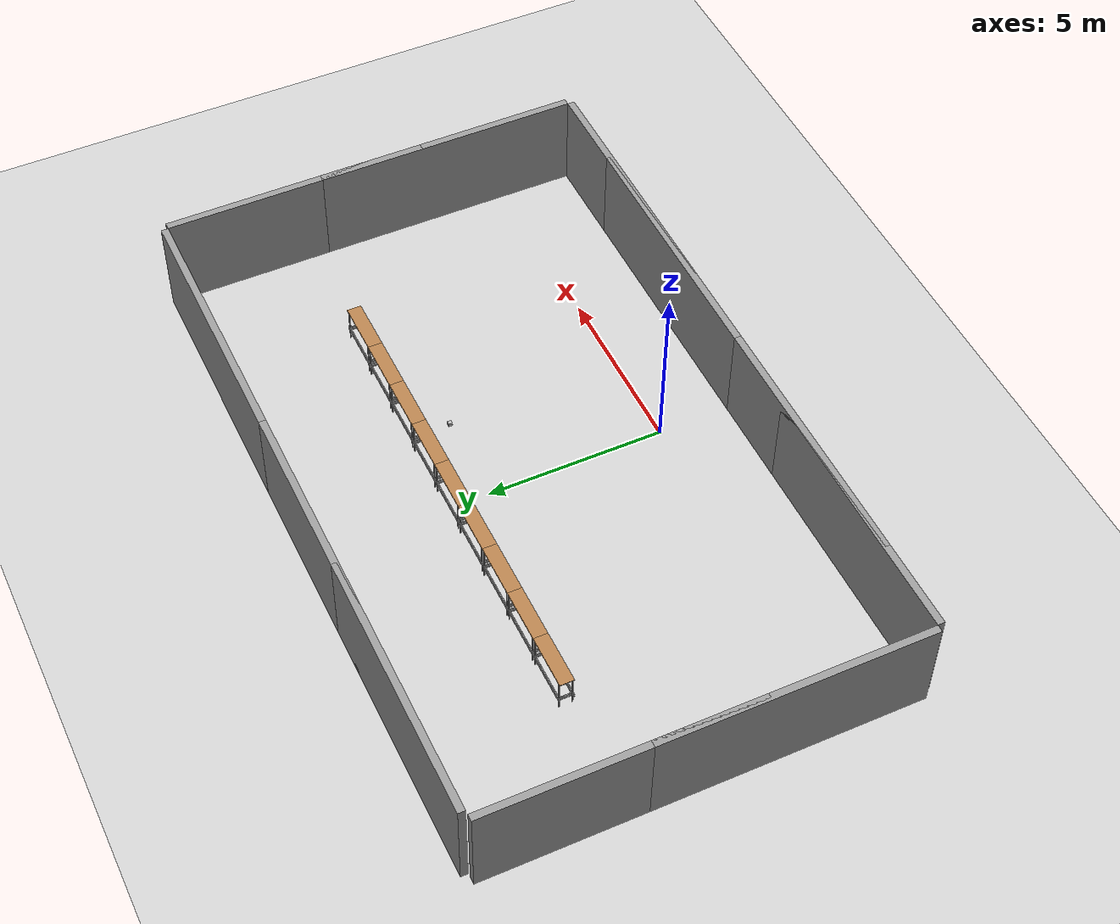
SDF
<sdf version="1.6">
 <world name="default">
  <plugin name="gazebo_occupancy_map" filename="libgazebo_2Dmap_plugin.so">
   <map_resolution>0.1</map_resolution>
   <map_height>2.8</map_height>
   <map_size_x>20</map_size_x>
   <map_size_y>20</map_size_y>
   <init_robot_x>0</init_robot_x>
   <init_robot_y>4</init_robot_y>
  </plugin>
  <light name="sun" type="directional">
   <cast_shadows>0</cast_shadows>
   <pose>0 0 10 0 -0 0</pose>
   <diffuse>0.8 0.8 0.8 1</diffuse>
   <specular>0.2 0.2 0.2 1</specular>
   <attenuation>
    <range>1000</range>
    <constant>0.9</constant>
    <linear>0.01</linear>
    <quadratic>0.001</quadratic>
   </attenuation>
   <direction>-0.5 0.1 -0.9</direction>
  </light>
  <model name="ground_plane">
   <static>1</static>
   <link name="link">
    <collision name="collision">
     <geometry><plane><normal>0 0 1</normal><size>100 100</size></plane></geometry>
     <surface>
      <contact><collide_bitmask>65535</collide_bitmask></contact>
      <friction><ode><mu>100</mu><mu2>50</mu2></ode></friction>
     </surface>
    </collision>
    <visual name="visual">
     <cast_shadows>0</cast_shadows>
     <geometry><plane><normal>0 0 1</normal><size>100 100</size></plane></geometry>
     <material>
      <script><uri>file://media/materials/scripts/gazebo.material</uri><name>Gazebo/Grey</name></script>
     </material>
    </visual>
   </link>
  </model>
  <gravity>0 0 -9.8</gravity>
  <magnetic_field>6e-06 2.3e-05 -4.2e-05</magnetic_field>
  <atmosphere type="adiabatic"/>
  <physics name="default_physics" default="0" type="ode">
   <max_step_size>0.001</max_step_size>
   <real_time_factor>1</real_time_factor>
   <real_time_update_rate>1000</real_time_update_rate>
  </physics>
  <scene><ambient>0.4 0.4 0.4 1</ambient><background>0.7 0.7 0.7 1</background><shadows>0</shadows></scene>
  <audio><device>default</device></audio>
  <spherical_coordinates>
   <surface_model>EARTH_WGS84</surface_model>
   <latitude_deg>0</latitude_deg>
   <longitude_deg>0</longitude_deg>
   <elevation>0</elevation>
   <heading_deg>0</heading_deg>
  </spherical_coordinates>
  <model name="grey_wall">
   <static>1</static>
   <link name="link">
    <pose>0 0 1.4 0 -0 0</pose>
    <collision name="collision"><geometry><box><size>7.5 0.2 2.8</size></box></geometry></collision>
    <visual name="visual">
     <cast_shadows>0</cast_shadows>
     <geometry><box><size>7.5 0.2 2.8</size></box></geometry>
     <material>
      <script>
       <uri>model://grey_wall/materials/scripts</uri>
       <uri>model://grey_wall/materials/textures</uri>
       <name>vrc/grey_wall</name>
      </script>
     </material>
    </visual>
   </link>
   <pose>-3.75 -2.1 0 0 -0 0</pose>
  </model>
  <model name="grey_wall_0">
   <static>1</static>
   <link name="link">
    <pose>0 0 1.4 0 -0 0</pose>
    <collision name="collision"><geometry><box><size>7.5 0.2 2.8</size></box></geometry></collision>
    <visual name="visual">
     <cast_shadows>0</cast_shadows>
     <geometry><box><size>7.5 0.2 2.8</size></box></geometry>
     <material>
      <script>
       <uri>model://grey_wall/materials/scripts</uri>
       <uri>model://grey_wall/materials/textures</uri>
       <name>vrc/grey_wall</name>
      </script>
     </material>
    </visual>
   </link>
   <pose>3.75 -2.1 0 0 -0 0</pose>
  </model>
  <model name="grey_wall_1">
   <static>1</static>
   <link name="link">
    <pose>0 0 1.4 0 -0 0</pose>
    <collision name="collision"><geometry><box><size>7.5 0.2 2.8</size></box></geometry></collision>
    <visual name="visual">
     <cast_shadows>0</cast_shadows>
     <geometry><box><size>7.5 0.2 2.8</size></box></geometry>
     <material>
      <script>
       <uri>model://grey_wall/materials/scripts</uri>
       <uri>model://grey_wall/materials/textures</uri>
       <name>vrc/grey_wall</name>
      </script>
     </material>
    </visual>
   </link>
   <pose>-6.25 -2.1 0 0 -0 0</pose>
  </model>
  <model name="grey_wall_2">
   <static>1</static>
   <link name="link">
    <pose>0 0 1.4 0 -0 0</pose>
    <collision name="collision"><geometry><box><size>7.5 0.2 2.8</size></box></geometry></collision>
    <visual name="visual">
     <cast_shadows>0</cast_shadows>
     <geometry><box><size>7.5 0.2 2.8</size></box></geometry>
     <material>
      <script>
       <uri>model://grey_wall/materials/scripts</uri>
       <uri>model://grey_wall/materials/textures</uri>
       <name>vrc/grey_wall</name>
      </script>
     </material>
    </visual>
   </link>
   <pose>6.25 -2.1 0 0 -0 0</pose>
  </model>
  <model name="grey_wall_3">
   <static>1</static>
   <link name="link">
    <pose>0 0 1.4 0 -0 0</pose>
    <collision name="collision"><geometry><box><size>7.5 0.2 2.8</size></box></geometry></collision>
    <visual name="visual">
     <cast_shadows>0</cast_shadows>
     <geometry><box><size>7.5 0.2 2.8</size></box></geometry>
     <material>
      <script>
       <uri>model://grey_wall/materials/scripts</uri>
       <uri>model://grey_wall/materials/textures</uri>
       <name>vrc/grey_wall</name>
      </script>
     </material>
    </visual>
   </link>
   <pose>-10.1 1.75 0 0 -0 1.5708</pose>
  </model>
  <model name="grey_wall_3_clone">
   <static>1</static>
   <link name="link">
    <pose>0 0 1.4 0 -0 0</pose>
    <collision name="collision"><geometry><box><size>7.5 0.2 2.8</size></box></geometry></collision>
    <visual name="visual">
     <cast_shadows>0</cast_shadows>
     <geometry><box><size>7.5 0.2 2.8</size></box></geometry>
     <material>
      <script>
       <uri>model://grey_wall/materials/scripts</uri>
       <uri>model://grey_wall/materials/textures</uri>
       <name>vrc/grey_wall</name>
      </script>
     </material>
    </visual>
   </link>
   <pose>-10.1 6.25 0 0 -0 1.5708</pose>
  </model>
  <model name="grey_wall_3_clone_clone">
   <static>1</static>
   <link name="link">
    <pose>0 0 1.4 0 -0 0</pose>
    <collision name="collision"><geometry><box><size>7.5 0.2 2.8</size></box></geometry></collision>
    <visual name="visual">
     <cast_shadows>0</cast_shadows>
     <geometry><box><size>7.5 0.2 2.8</size></box></geometry>
     <material>
      <script>
       <uri>model://grey_wall/materials/scripts</uri>
       <uri>model://grey_wall/materials/textures</uri>
       <name>vrc/grey_wall</name>
      </script>
     </material>
    </visual>
   </link>
   <pose>10.1 6.25 0 0 -0 1.5708</pose>
  </model>
  <model name="grey_wall_3_clone_clone_0">
   <static>1</static>
   <link name="link">
    <pose>0 0 1.4 0 -0 0</pose>
    <collision name="collision"><geometry><box><size>7.5 0.2 2.8</size></box></geometry></collision>
    <visual name="visual">
     <cast_shadows>0</cast_shadows>
     <geometry><box><size>7.5 0.2 2.8</size></box></geometry>
     <material>
      <script>
       <uri>model://grey_wall/materials/scripts</uri>
       <uri>model://grey_wall/materials/textures</uri>
       <name>vrc/grey_wall</name>
      </script>
     </material>
    </visual>
   </link>
   <pose>10.1 1.75 0 0 -0 1.5708</pose>
  </model>
  <model name="grey_wall_1_clone">
   <static>1</static>
   <link name="link">
    <pose>0 0 1.4 0 -0 0</pose>
    <collision name="collision"><geometry><box><size>7.5 0.2 2.8</size></box></geometry></collision>
    <visual name="visual">
     <cast_shadows>0</cast_shadows>
     <geometry><box><size>7.5 0.2 2.8</size></box></geometry>
     <material>
      <script>
       <uri>model://grey_wall/materials/scripts</uri>
       <uri>model://grey_wall/materials/textures</uri>
       <name>vrc/grey_wall</name>
      </script>
     </material>
    </visual>
   </link>
   <pose>-6.15 10.1 0 0 -0 0</pose>
  </model>
  <model name="grey_wall_clone">
   <static>1</static>
   <link name="link">
    <pose>0 0 1.4 0 -0 0</pose>
    <collision name="collision"><geometry><box><size>7.5 0.2 2.8</size></box></geometry></collision>
    <visual name="visual">
     <cast_shadows>0</cast_shadows>
     <geometry><box><size>7.5 0.2 2.8</size></box></geometry>
     <material>
      <script>
       <uri>model://grey_wall/materials/scripts</uri>
       <uri>model://grey_wall/materials/textures</uri>
       <name>vrc/grey_wall</name>
      </script>
     </material>
    </visual>
   </link>
   <pose>0 10.1 0 0 -0 0</pose>
  </model>
  <model name="grey_wall_clone_0">
   <static>1</static>
   <link name="link">
    <pose>0 0 1.4 0 -0 0</pose>
    <collision name="collision"><geometry><box><size>7.5 0.2 2.8</size></box></geometry></collision>
    <visual name="visual">
     <cast_shadows>0</cast_shadows>
     <geometry><box><size>7.5 0.2 2.8</size></box></geometry>
     <material>
      <script>
       <uri>model://grey_wall/materials/scripts</uri>
       <uri>model://grey_wall/materials/textures</uri>
       <name>vrc/grey_wall</name>
      </script>
     </material>
    </visual>
   </link>
   <pose>6.25 10.1 0 0 -0 0</pose>
  </model>
  <model name="distorted_camera">
   <link name="link">
    <pose>0.05 0.05 0.05 0 -0 0</pose>
    <inertial>
     <mass>0.1</mass>
     <inertia>
      <ixx>0.000166667</ixx>
      <iyy>0.000166667</iyy>
      <izz>0.000166667</izz>
      <ixy>0</ixy>
      <ixz>0</ixz>
      <iyz>0</iyz>
     </inertia>
    </inertial>
    <collision name="collision"><geometry><box><size>0.1 0.1 0.1</size></box></geometry></collision>
    <visual name="visual"><geometry><box><size>0.1 0.1 0.1</size></box></geometry></visual>
    <gravity>0</gravity>
    <sensor name="camera" type="camera">
     <camera name="__default__">
      <horizontal_fov>1.047</horizontal_fov>
      <image><width>64</width><height>64</height></image>
      <clip><near>0.1</near><far>100</far></clip>
     </camera>
     <plugin name="camera_controller" filename="libgazebo_ros_camera.so">
      <alwaysOn>1</alwaysOn>
      <updateRate>0.0</updateRate>
      <cameraName>top_down_cam</cameraName>
      <imageTopicName>image_raw</imageTopicName>
      <cameraInfoTopicName>camera_info</cameraInfoTopicName>
      <frameName>camera_link</frameName>
      <hackBaseline>0.07</hackBaseline>
      <distortionK1>0.0</distortionK1>
      <distortionK2>0.0</distortionK2>
      <distortionK3>0.0</distortionK3>
      <distortionT1>0.0</distortionT1>
      <distortionT2>0.0</distortionT2>
     </plugin>
     <always_on>1</always_on>
     <update_rate>30</update_rate>
     <visualize>1</visualize>
    </sensor>
   </link>
   <pose>0 6 3.46489 0 1.57 1.57</pose>
  </model>
  <model name="table_4">
   <static>1</static>
   <link name="link">
    <collision name="surface">
     <pose>0 0 1 0 -0 0</pose>
     <geometry><box><size>1.5 0.4 0.03</size></box></geometry>
     <surface><friction><ode><mu>0.6</mu><mu2>0.6</mu2></ode></friction></surface>
    </collision>
    <visual name="visual1">
     <pose>0 0 1 0 -0 0</pose>
     <geometry><box><size>1.5 0.4 0.03</size></box></geometry>
     <material>
      <script><uri>file://media/materials/scripts/gazebo.material</uri><name>Gazebo/Wood</name></script>
     </material>
    </visual>
    <collision name="front_left_leg">
     <pose>0.68 0.18 0.5 0 -0 0</pose>
     <geometry><cylinder><radius>0.02</radius><length>1</length></cylinder></geometry>
    </collision>
    <visual name="front_left_leg">
     <pose>0.68 0.18 0.5 0 -0 0</pose>
     <geometry><cylinder><radius>0.02</radius><length>1</length></cylinder></geometry>
     <material>
      <script><uri>file://media/materials/scripts/gazebo.material</uri><name>Gazebo/Grey</name></script>
     </material>
    </visual>
    <collision name="front_right_leg">
     <pose>0.68 -0.18 0.5 0 -0 0</pose>
     <geometry><cylinder><radius>0.02</radius><length>1</length></cylinder></geometry>
    </collision>
    <visual name="front_right_leg">
     <pose>0.68 -0.18 0.5 0 -0 0</pose>
     <geometry><cylinder><radius>0.02</radius><length>1</length></cylinder></geometry>
     <material>
      <script><uri>file://media/materials/scripts/gazebo.material</uri><name>Gazebo/Grey</name></script>
     </material>
    </visual>
    <collision name="back_right_leg">
     <pose>-0.68 -0.18 0.5 0 -0 0</pose>
     <geometry><cylinder><radius>0.02</radius><length>1</length></cylinder></geometry>
    </collision>
    <visual name="back_right_leg">
     <pose>-0.68 -0.18 0.5 0 -0 0</pose>
     <geometry><cylinder><radius>0.02</radius><length>1</length></cylinder></geometry>
     <material>
      <script><uri>file://media/materials/scripts/gazebo.material</uri><name>Gazebo/Grey</name></script>
     </material>
    </visual>
    <collision name="back_left_leg">
     <pose>-0.68 0.18 0.5 0 -0 0</pose>
     <geometry><cylinder><radius>0.02</radius><length>1</length></cylinder></geometry>
    </collision>
    <visual name="back_left_leg">
     <pose>-0.68 0.18 0.5 0 -0 0</pose>
     <geometry><cylinder><radius>0.02</radius><length>1</length></cylinder></geometry>
     <material>
      <script><uri>file://media/materials/scripts/gazebo.material</uri><name>Gazebo/Grey</name></script>
     </material>
    </visual>
    <collision name="back_leg_connector">
     <pose>0 -0.19 0.38 0 1.57 0</pose>
     <geometry><cylinder><radius>0.02</radius><length>1.5</length></cylinder></geometry>
    </collision>
    <visual name="back_leg_connector">
     <pose>0 -0.19 0.38 0 1.57 0</pose>
     <geometry><cylinder><radius>0.02</radius><length>1.5</length></cylinder></geometry>
     <material>
      <script><uri>file://media/materials/scripts/gazebo.material</uri><name>Gazebo/Grey</name></script>
     </material>
    </visual>
    <collision name="front_leg_connector">
     <pose>0 0.19 0.38 0 1.57 0</pose>
     <geometry><cylinder><radius>0.02</radius><length>1.5</length></cylinder></geometry>
    </collision>
    <visual name="front_leg_connector">
     <pose>0 0.19 0.38 0 1.57 0</pose>
     <geometry><cylinder><radius>0.02</radius><length>1.5</length></cylinder></geometry>
     <material>
      <script><uri>file://media/materials/scripts/gazebo.material</uri><name>Gazebo/Grey</name></script>
     </material>
    </visual>
    <collision name="right_leg_connector">
     <pose>-0.68 0 0.38 0 1.57 1.57</pose>
     <geometry><cylinder><radius>0.02</radius><length>0.36</length></cylinder></geometry>
    </collision>
    <visual name="right_leg_connector">
     <pose>-0.68 0 0.38 0 1.57 1.57</pose>
     <geometry><cylinder><radius>0.02</radius><length>0.36</length></cylinder></geometry>
     <material>
      <script><uri>file://media/materials/scripts/gazebo.material</uri><name>Gazebo/Grey</name></script>
     </material>
    </visual>
    <collision name="left_leg_connector">
     <pose>0.68 0 0.38 0 1.57 1.57</pose>
     <geometry><cylinder><radius>0.02</radius><length>0.36</length></cylinder></geometry>
    </collision>
    <visual name="left_leg_connector">
     <pose>0.68 0 0.38 0 1.57 1.57</pose>
     <geometry><cylinder><radius>0.02</radius><length>0.36</length></cylinder></geometry>
     <material>
      <script><uri>file://media/materials/scripts/gazebo.material</uri><name>Gazebo/Grey</name></script>
     </material>
    </visual>
    <collision name="back_leg_connector1">
     <pose>0 -0.19 0.3 0 1.57 0</pose>
     <geometry><cylinder><radius>0.02</radius><length>1.5</length></cylinder></geometry>
    </collision>
    <visual name="back_leg_connector1">
     <pose>0 -0.19 0.3 0 1.57 0</pose>
     <geometry><cylinder><radius>0.02</radius><length>1.5</length></cylinder></geometry>
     <material>
      <script><uri>file://media/materials/scripts/gazebo.material</uri><name>Gazebo/Grey</name></script>
     </material>
    </visual>
    <collision name="front_leg_connector1">
     <pose>0 0.19 0.3 0 1.57 0</pose>
     <geometry><cylinder><radius>0.02</radius><length>1.5</length></cylinder></geometry>
    </collision>
    <visual name="front_leg_connector1">
     <pose>0 0.19 0.3 0 1.57 0</pose>
     <geometry><cylinder><radius>0.02</radius><length>1.5</length></cylinder></geometry>
     <material>
      <script><uri>file://media/materials/scripts/gazebo.material</uri><name>Gazebo/Grey</name></script>
     </material>
    </visual>
    <collision name="right_leg_connector1">
     <pose>-0.68 0 0.3 0 1.57 1.57</pose>
     <geometry><cylinder><radius>0.02</radius><length>0.36</length></cylinder></geometry>
    </collision>
    <visual name="right_leg_connector1">
     <pose>-0.68 0 0.3 0 1.57 1.57</pose>
     <geometry><cylinder><radius>0.02</radius><length>0.36</length></cylinder></geometry>
     <material>
      <script><uri>file://media/materials/scripts/gazebo.material</uri><name>Gazebo/Grey</name></script>
     </material>
    </visual>
    <collision name="left_leg_connector1">
     <pose>0.68 0 0.3 0 1.57 1.57</pose>
     <geometry><cylinder><radius>0.02</radius><length>0.36</length></cylinder></geometry>
    </collision>
    <visual name="left_leg_connector1">
     <pose>0.68 0 0.3 0 1.57 1.57</pose>
     <geometry><cylinder><radius>0.02</radius><length>0.36</length></cylinder></geometry>
     <material>
      <script><uri>file://media/materials/scripts/gazebo.material</uri><name>Gazebo/Grey</name></script>
     </material>
    </visual>
   </link>
   <pose>1.5 6 0 0 -0 0</pose>
  </model>
  <model name="table_5">
   <static>1</static>
   <link name="link">
    <collision name="surface">
     <pose>0 0 1 0 -0 0</pose>
     <geometry><box><size>1.5 0.4 0.03</size></box></geometry>
     <surface><friction><ode><mu>0.6</mu><mu2>0.6</mu2></ode></friction></surface>
    </collision>
    <visual name="visual1">
     <pose>0 0 1 0 -0 0</pose>
     <geometry><box><size>1.5 0.4 0.03</size></box></geometry>
     <material>
      <script><uri>file://media/materials/scripts/gazebo.material</uri><name>Gazebo/Wood</name></script>
     </material>
    </visual>
    <collision name="front_left_leg">
     <pose>0.68 0.18 0.5 0 -0 0</pose>
     <geometry><cylinder><radius>0.02</radius><length>1</length></cylinder></geometry>
    </collision>
    <visual name="front_left_leg">
     <pose>0.68 0.18 0.5 0 -0 0</pose>
     <geometry><cylinder><radius>0.02</radius><length>1</length></cylinder></geometry>
     <material>
      <script><uri>file://media/materials/scripts/gazebo.material</uri><name>Gazebo/Grey</name></script>
     </material>
    </visual>
    <collision name="front_right_leg">
     <pose>0.68 -0.18 0.5 0 -0 0</pose>
     <geometry><cylinder><radius>0.02</radius><length>1</length></cylinder></geometry>
    </collision>
    <visual name="front_right_leg">
     <pose>0.68 -0.18 0.5 0 -0 0</pose>
     <geometry><cylinder><radius>0.02</radius><length>1</length></cylinder></geometry>
     <material>
      <script><uri>file://media/materials/scripts/gazebo.material</uri><name>Gazebo/Grey</name></script>
     </material>
    </visual>
    <collision name="back_right_leg">
     <pose>-0.68 -0.18 0.5 0 -0 0</pose>
     <geometry><cylinder><radius>0.02</radius><length>1</length></cylinder></geometry>
    </collision>
    <visual name="back_right_leg">
     <pose>-0.68 -0.18 0.5 0 -0 0</pose>
     <geometry><cylinder><radius>0.02</radius><length>1</length></cylinder></geometry>
     <material>
      <script><uri>file://media/materials/scripts/gazebo.material</uri><name>Gazebo/Grey</name></script>
     </material>
    </visual>
    <collision name="back_left_leg">
     <pose>-0.68 0.18 0.5 0 -0 0</pose>
     <geometry><cylinder><radius>0.02</radius><length>1</length></cylinder></geometry>
    </collision>
    <visual name="back_left_leg">
     <pose>-0.68 0.18 0.5 0 -0 0</pose>
     <geometry><cylinder><radius>0.02</radius><length>1</length></cylinder></geometry>
     <material>
      <script><uri>file://media/materials/scripts/gazebo.material</uri><name>Gazebo/Grey</name></script>
     </material>
    </visual>
    <collision name="back_leg_connector">
     <pose>0 -0.19 0.38 0 1.57 0</pose>
     <geometry><cylinder><radius>0.02</radius><length>1.5</length></cylinder></geometry>
    </collision>
    <visual name="back_leg_connector">
     <pose>0 -0.19 0.38 0 1.57 0</pose>
     <geometry><cylinder><radius>0.02</radius><length>1.5</length></cylinder></geometry>
     <material>
      <script><uri>file://media/materials/scripts/gazebo.material</uri><name>Gazebo/Grey</name></script>
     </material>
    </visual>
    <collision name="front_leg_connector">
     <pose>0 0.19 0.38 0 1.57 0</pose>
     <geometry><cylinder><radius>0.02</radius><length>1.5</length></cylinder></geometry>
    </collision>
    <visual name="front_leg_connector">
     <pose>0 0.19 0.38 0 1.57 0</pose>
     <geometry><cylinder><radius>0.02</radius><length>1.5</length></cylinder></geometry>
     <material>
      <script><uri>file://media/materials/scripts/gazebo.material</uri><name>Gazebo/Grey</name></script>
     </material>
    </visual>
    <collision name="right_leg_connector">
     <pose>-0.68 0 0.38 0 1.57 1.57</pose>
     <geometry><cylinder><radius>0.02</radius><length>0.36</length></cylinder></geometry>
    </collision>
    <visual name="right_leg_connector">
     <pose>-0.68 0 0.38 0 1.57 1.57</pose>
     <geometry><cylinder><radius>0.02</radius><length>0.36</length></cylinder></geometry>
     <material>
      <script><uri>file://media/materials/scripts/gazebo.material</uri><name>Gazebo/Grey</name></script>
     </material>
    </visual>
    <collision name="left_leg_connector">
     <pose>0.68 0 0.38 0 1.57 1.57</pose>
     <geometry><cylinder><radius>0.02</radius><length>0.36</length></cylinder></geometry>
    </collision>
    <visual name="left_leg_connector">
     <pose>0.68 0 0.38 0 1.57 1.57</pose>
     <geometry><cylinder><radius>0.02</radius><length>0.36</length></cylinder></geometry>
     <material>
      <script><uri>file://media/materials/scripts/gazebo.material</uri><name>Gazebo/Grey</name></script>
     </material>
    </visual>
    <collision name="back_leg_connector1">
     <pose>0 -0.19 0.3 0 1.57 0</pose>
     <geometry><cylinder><radius>0.02</radius><length>1.5</length></cylinder></geometry>
    </collision>
    <visual name="back_leg_connector1">
     <pose>0 -0.19 0.3 0 1.57 0</pose>
     <geometry><cylinder><radius>0.02</radius><length>1.5</length></cylinder></geometry>
     <material>
      <script><uri>file://media/materials/scripts/gazebo.material</uri><name>Gazebo/Grey</name></script>
     </material>
    </visual>
    <collision name="front_leg_connector1">
     <pose>0 0.19 0.3 0 1.57 0</pose>
     <geometry><cylinder><radius>0.02</radius><length>1.5</length></cylinder></geometry>
    </collision>
    <visual name="front_leg_connector1">
     <pose>0 0.19 0.3 0 1.57 0</pose>
     <geometry><cylinder><radius>0.02</radius><length>1.5</length></cylinder></geometry>
     <material>
      <script><uri>file://media/materials/scripts/gazebo.material</uri><name>Gazebo/Grey</name></script>
     </material>
    </visual>
    <collision name="right_leg_connector1">
     <pose>-0.68 0 0.3 0 1.57 1.57</pose>
     <geometry><cylinder><radius>0.02</radius><length>0.36</length></cylinder></geometry>
    </collision>
    <visual name="right_leg_connector1">
     <pose>-0.68 0 0.3 0 1.57 1.57</pose>
     <geometry><cylinder><radius>0.02</radius><length>0.36</length></cylinder></geometry>
     <material>
      <script><uri>file://media/materials/scripts/gazebo.material</uri><name>Gazebo/Grey</name></script>
     </material>
    </visual>
    <collision name="left_leg_connector1">
     <pose>0.68 0 0.3 0 1.57 1.57</pose>
     <geometry><cylinder><radius>0.02</radius><length>0.36</length></cylinder></geometry>
    </collision>
    <visual name="left_leg_connector1">
     <pose>0.68 0 0.3 0 1.57 1.57</pose>
     <geometry><cylinder><radius>0.02</radius><length>0.36</length></cylinder></geometry>
     <material>
      <script><uri>file://media/materials/scripts/gazebo.material</uri><name>Gazebo/Grey</name></script>
     </material>
    </visual>
   </link>
   <pose>3 6 0 0 -0 0</pose>
  </model>
  <model name="table_6">
   <static>1</static>
   <link name="link">
    <collision name="surface">
     <pose>0 0 1 0 -0 0</pose>
     <geometry><box><size>1.5 0.4 0.03</size></box></geometry>
     <surface><friction><ode><mu>0.6</mu><mu2>0.6</mu2></ode></friction></surface>
    </collision>
    <visual name="visual1">
     <pose>0 0 1 0 -0 0</pose>
     <geometry><box><size>1.5 0.4 0.03</size></box></geometry>
     <material>
      <script><uri>file://media/materials/scripts/gazebo.material</uri><name>Gazebo/Wood</name></script>
     </material>
    </visual>
    <collision name="front_left_leg">
     <pose>0.68 0.18 0.5 0 -0 0</pose>
     <geometry><cylinder><radius>0.02</radius><length>1</length></cylinder></geometry>
    </collision>
    <visual name="front_left_leg">
     <pose>0.68 0.18 0.5 0 -0 0</pose>
     <geometry><cylinder><radius>0.02</radius><length>1</length></cylinder></geometry>
     <material>
      <script><uri>file://media/materials/scripts/gazebo.material</uri><name>Gazebo/Grey</name></script>
     </material>
    </visual>
    <collision name="front_right_leg">
     <pose>0.68 -0.18 0.5 0 -0 0</pose>
     <geometry><cylinder><radius>0.02</radius><length>1</length></cylinder></geometry>
    </collision>
    <visual name="front_right_leg">
     <pose>0.68 -0.18 0.5 0 -0 0</pose>
     <geometry><cylinder><radius>0.02</radius><length>1</length></cylinder></geometry>
     <material>
      <script><uri>file://media/materials/scripts/gazebo.material</uri><name>Gazebo/Grey</name></script>
     </material>
    </visual>
    <collision name="back_right_leg">
     <pose>-0.68 -0.18 0.5 0 -0 0</pose>
     <geometry><cylinder><radius>0.02</radius><length>1</length></cylinder></geometry>
    </collision>
    <visual name="back_right_leg">
     <pose>-0.68 -0.18 0.5 0 -0 0</pose>
     <geometry><cylinder><radius>0.02</radius><length>1</length></cylinder></geometry>
     <material>
      <script><uri>file://media/materials/scripts/gazebo.material</uri><name>Gazebo/Grey</name></script>
     </material>
    </visual>
    <collision name="back_left_leg">
     <pose>-0.68 0.18 0.5 0 -0 0</pose>
     <geometry><cylinder><radius>0.02</radius><length>1</length></cylinder></geometry>
    </collision>
    <visual name="back_left_leg">
     <pose>-0.68 0.18 0.5 0 -0 0</pose>
     <geometry><cylinder><radius>0.02</radius><length>1</length></cylinder></geometry>
     <material>
      <script><uri>file://media/materials/scripts/gazebo.material</uri><name>Gazebo/Grey</name></script>
     </material>
    </visual>
    <collision name="back_leg_connector">
     <pose>0 -0.19 0.38 0 1.57 0</pose>
     <geometry><cylinder><radius>0.02</radius><length>1.5</length></cylinder></geometry>
    </collision>
    <visual name="back_leg_connector">
     <pose>0 -0.19 0.38 0 1.57 0</pose>
     <geometry><cylinder><radius>0.02</radius><length>1.5</length></cylinder></geometry>
     <material>
      <script><uri>file://media/materials/scripts/gazebo.material</uri><name>Gazebo/Grey</name></script>
     </material>
    </visual>
    <collision name="front_leg_connector">
     <pose>0 0.19 0.38 0 1.57 0</pose>
     <geometry><cylinder><radius>0.02</radius><length>1.5</length></cylinder></geometry>
    </collision>
    <visual name="front_leg_connector">
     <pose>0 0.19 0.38 0 1.57 0</pose>
     <geometry><cylinder><radius>0.02</radius><length>1.5</length></cylinder></geometry>
     <material>
      <script><uri>file://media/materials/scripts/gazebo.material</uri><name>Gazebo/Grey</name></script>
     </material>
    </visual>
    <collision name="right_leg_connector">
     <pose>-0.68 0 0.38 0 1.57 1.57</pose>
     <geometry><cylinder><radius>0.02</radius><length>0.36</length></cylinder></geometry>
    </collision>
    <visual name="right_leg_connector">
     <pose>-0.68 0 0.38 0 1.57 1.57</pose>
     <geometry><cylinder><radius>0.02</radius><length>0.36</length></cylinder></geometry>
     <material>
      <script><uri>file://media/materials/scripts/gazebo.material</uri><name>Gazebo/Grey</name></script>
     </material>
    </visual>
    <collision name="left_leg_connector">
     <pose>0.68 0 0.38 0 1.57 1.57</pose>
     <geometry><cylinder><radius>0.02</radius><length>0.36</length></cylinder></geometry>
    </collision>
    <visual name="left_leg_connector">
     <pose>0.68 0 0.38 0 1.57 1.57</pose>
     <geometry><cylinder><radius>0.02</radius><length>0.36</length></cylinder></geometry>
     <material>
      <script><uri>file://media/materials/scripts/gazebo.material</uri><name>Gazebo/Grey</name></script>
     </material>
    </visual>
    <collision name="back_leg_connector1">
     <pose>0 -0.19 0.3 0 1.57 0</pose>
     <geometry><cylinder><radius>0.02</radius><length>1.5</length></cylinder></geometry>
    </collision>
    <visual name="back_leg_connector1">
     <pose>0 -0.19 0.3 0 1.57 0</pose>
     <geometry><cylinder><radius>0.02</radius><length>1.5</length></cylinder></geometry>
     <material>
      <script><uri>file://media/materials/scripts/gazebo.material</uri><name>Gazebo/Grey</name></script>
     </material>
    </visual>
    <collision name="front_leg_connector1">
     <pose>0 0.19 0.3 0 1.57 0</pose>
     <geometry><cylinder><radius>0.02</radius><length>1.5</length></cylinder></geometry>
    </collision>
    <visual name="front_leg_connector1">
     <pose>0 0.19 0.3 0 1.57 0</pose>
     <geometry><cylinder><radius>0.02</radius><length>1.5</length></cylinder></geometry>
     <material>
      <script><uri>file://media/materials/scripts/gazebo.material</uri><name>Gazebo/Grey</name></script>
     </material>
    </visual>
    <collision name="right_leg_connector1">
     <pose>-0.68 0 0.3 0 1.57 1.57</pose>
     <geometry><cylinder><radius>0.02</radius><length>0.36</length></cylinder></geometry>
    </collision>
    <visual name="right_leg_connector1">
     <pose>-0.68 0 0.3 0 1.57 1.57</pose>
     <geometry><cylinder><radius>0.02</radius><length>0.36</length></cylinder></geometry>
     <material>
      <script><uri>file://media/materials/scripts/gazebo.material</uri><name>Gazebo/Grey</name></script>
     </material>
    </visual>
    <collision name="left_leg_connector1">
     <pose>0.68 0 0.3 0 1.57 1.57</pose>
     <geometry><cylinder><radius>0.02</radius><length>0.36</length></cylinder></geometry>
    </collision>
    <visual name="left_leg_connector1">
     <pose>0.68 0 0.3 0 1.57 1.57</pose>
     <geometry><cylinder><radius>0.02</radius><length>0.36</length></cylinder></geometry>
     <material>
      <script><uri>file://media/materials/scripts/gazebo.material</uri><name>Gazebo/Grey</name></script>
     </material>
    </visual>
   </link>
   <pose>4.5 6 0 0 -0 0</pose>
  </model>
  <model name="table_7">
   <static>1</static>
   <link name="link">
    <collision name="surface">
     <pose>0 0 1 0 -0 0</pose>
     <geometry><box><size>1.5 0.4 0.03</size></box></geometry>
     <surface><friction><ode><mu>0.6</mu><mu2>0.6</mu2></ode></friction></surface>
    </collision>
    <visual name="visual1">
     <pose>0 0 1 0 -0 0</pose>
     <geometry><box><size>1.5 0.4 0.03</size></box></geometry>
     <material>
      <script><uri>file://media/materials/scripts/gazebo.material</uri><name>Gazebo/Wood</name></script>
     </material>
    </visual>
    <collision name="front_left_leg">
     <pose>0.68 0.18 0.5 0 -0 0</pose>
     <geometry><cylinder><radius>0.02</radius><length>1</length></cylinder></geometry>
    </collision>
    <visual name="front_left_leg">
     <pose>0.68 0.18 0.5 0 -0 0</pose>
     <geometry><cylinder><radius>0.02</radius><length>1</length></cylinder></geometry>
     <material>
      <script><uri>file://media/materials/scripts/gazebo.material</uri><name>Gazebo/Grey</name></script>
     </material>
    </visual>
    <collision name="front_right_leg">
     <pose>0.68 -0.18 0.5 0 -0 0</pose>
     <geometry><cylinder><radius>0.02</radius><length>1</length></cylinder></geometry>
    </collision>
    <visual name="front_right_leg">
     <pose>0.68 -0.18 0.5 0 -0 0</pose>
     <geometry><cylinder><radius>0.02</radius><length>1</length></cylinder></geometry>
     <material>
      <script><uri>file://media/materials/scripts/gazebo.material</uri><name>Gazebo/Grey</name></script>
     </material>
    </visual>
    <collision name="back_right_leg">
     <pose>-0.68 -0.18 0.5 0 -0 0</pose>
     <geometry><cylinder><radius>0.02</radius><length>1</length></cylinder></geometry>
    </collision>
    <visual name="back_right_leg">
     <pose>-0.68 -0.18 0.5 0 -0 0</pose>
     <geometry><cylinder><radius>0.02</radius><length>1</length></cylinder></geometry>
     <material>
      <script><uri>file://media/materials/scripts/gazebo.material</uri><name>Gazebo/Grey</name></script>
     </material>
    </visual>
    <collision name="back_left_leg">
     <pose>-0.68 0.18 0.5 0 -0 0</pose>
     <geometry><cylinder><radius>0.02</radius><length>1</length></cylinder></geometry>
    </collision>
    <visual name="back_left_leg">
     <pose>-0.68 0.18 0.5 0 -0 0</pose>
     <geometry><cylinder><radius>0.02</radius><length>1</length></cylinder></geometry>
     <material>
      <script><uri>file://media/materials/scripts/gazebo.material</uri><name>Gazebo/Grey</name></script>
     </material>
    </visual>
    <collision name="back_leg_connector">
     <pose>0 -0.19 0.38 0 1.57 0</pose>
     <geometry><cylinder><radius>0.02</radius><length>1.5</length></cylinder></geometry>
    </collision>
    <visual name="back_leg_connector">
     <pose>0 -0.19 0.38 0 1.57 0</pose>
     <geometry><cylinder><radius>0.02</radius><length>1.5</length></cylinder></geometry>
     <material>
      <script><uri>file://media/materials/scripts/gazebo.material</uri><name>Gazebo/Grey</name></script>
     </material>
    </visual>
    <collision name="front_leg_connector">
     <pose>0 0.19 0.38 0 1.57 0</pose>
     <geometry><cylinder><radius>0.02</radius><length>1.5</length></cylinder></geometry>
    </collision>
    <visual name="front_leg_connector">
     <pose>0 0.19 0.38 0 1.57 0</pose>
     <geometry><cylinder><radius>0.02</radius><length>1.5</length></cylinder></geometry>
     <material>
      <script><uri>file://media/materials/scripts/gazebo.material</uri><name>Gazebo/Grey</name></script>
     </material>
    </visual>
    <collision name="right_leg_connector">
     <pose>-0.68 0 0.38 0 1.57 1.57</pose>
     <geometry><cylinder><radius>0.02</radius><length>0.36</length></cylinder></geometry>
    </collision>
    <visual name="right_leg_connector">
     <pose>-0.68 0 0.38 0 1.57 1.57</pose>
     <geometry><cylinder><radius>0.02</radius><length>0.36</length></cylinder></geometry>
     <material>
      <script><uri>file://media/materials/scripts/gazebo.material</uri><name>Gazebo/Grey</name></script>
     </material>
    </visual>
    <collision name="left_leg_connector">
     <pose>0.68 0 0.38 0 1.57 1.57</pose>
     <geometry><cylinder><radius>0.02</radius><length>0.36</length></cylinder></geometry>
    </collision>
    <visual name="left_leg_connector">
     <pose>0.68 0 0.38 0 1.57 1.57</pose>
     <geometry><cylinder><radius>0.02</radius><length>0.36</length></cylinder></geometry>
     <material>
      <script><uri>file://media/materials/scripts/gazebo.material</uri><name>Gazebo/Grey</name></script>
     </material>
    </visual>
    <collision name="back_leg_connector1">
     <pose>0 -0.19 0.3 0 1.57 0</pose>
     <geometry><cylinder><radius>0.02</radius><length>1.5</length></cylinder></geometry>
    </collision>
    <visual name="back_leg_connector1">
     <pose>0 -0.19 0.3 0 1.57 0</pose>
     <geometry><cylinder><radius>0.02</radius><length>1.5</length></cylinder></geometry>
     <material>
      <script><uri>file://media/materials/scripts/gazebo.material</uri><name>Gazebo/Grey</name></script>
     </material>
    </visual>
    <collision name="front_leg_connector1">
     <pose>0 0.19 0.3 0 1.57 0</pose>
     <geometry><cylinder><radius>0.02</radius><length>1.5</length></cylinder></geometry>
    </collision>
    <visual name="front_leg_connector1">
     <pose>0 0.19 0.3 0 1.57 0</pose>
     <geometry><cylinder><radius>0.02</radius><length>1.5</length></cylinder></geometry>
     <material>
      <script><uri>file://media/materials/scripts/gazebo.material</uri><name>Gazebo/Grey</name></script>
     </material>
    </visual>
    <collision name="right_leg_connector1">
     <pose>-0.68 0 0.3 0 1.57 1.57</pose>
     <geometry><cylinder><radius>0.02</radius><length>0.36</length></cylinder></geometry>
    </collision>
    <visual name="right_leg_connector1">
     <pose>-0.68 0 0.3 0 1.57 1.57</pose>
     <geometry><cylinder><radius>0.02</radius><length>0.36</length></cylinder></geometry>
     <material>
      <script><uri>file://media/materials/scripts/gazebo.material</uri><name>Gazebo/Grey</name></script>
     </material>
    </visual>
    <collision name="left_leg_connector1">
     <pose>0.68 0 0.3 0 1.57 1.57</pose>
     <geometry><cylinder><radius>0.02</radius><length>0.36</length></cylinder></geometry>
    </collision>
    <visual name="left_leg_connector1">
     <pose>0.68 0 0.3 0 1.57 1.57</pose>
     <geometry><cylinder><radius>0.02</radius><length>0.36</length></cylinder></geometry>
     <material>
      <script><uri>file://media/materials/scripts/gazebo.material</uri><name>Gazebo/Grey</name></script>
     </material>
    </visual>
   </link>
   <pose>6 6 0 0 -0 0</pose>
  </model>
  <model name="table">
   <static>1</static>
   <link name="link">
    <collision name="surface">
     <pose>0 0 1 0 -0 0</pose>
     <geometry><box><size>1.5 0.4 0.03</size></box></geometry>
     <surface><friction><ode><mu>0.6</mu><mu2>0.6</mu2></ode></friction></surface>
    </collision>
    <visual name="visual1">
     <pose>0 0 1 0 -0 0</pose>
     <geometry><box><size>1.5 0.4 0.03</size></box></geometry>
     <material>
      <script><uri>file://media/materials/scripts/gazebo.material</uri><name>Gazebo/Wood</name></script>
     </material>
    </visual>
    <collision name="front_left_leg">
     <pose>0.68 0.18 0.5 0 -0 0</pose>
     <geometry><cylinder><radius>0.02</radius><length>1</length></cylinder></geometry>
    </collision>
    <visual name="front_left_leg">
     <pose>0.68 0.18 0.5 0 -0 0</pose>
     <geometry><cylinder><radius>0.02</radius><length>1</length></cylinder></geometry>
     <material>
      <script><uri>file://media/materials/scripts/gazebo.material</uri><name>Gazebo/Grey</name></script>
     </material>
    </visual>
    <collision name="front_right_leg">
     <pose>0.68 -0.18 0.5 0 -0 0</pose>
     <geometry><cylinder><radius>0.02</radius><length>1</length></cylinder></geometry>
    </collision>
    <visual name="front_right_leg">
     <pose>0.68 -0.18 0.5 0 -0 0</pose>
     <geometry><cylinder><radius>0.02</radius><length>1</length></cylinder></geometry>
     <material>
      <script><uri>file://media/materials/scripts/gazebo.material</uri><name>Gazebo/Grey</name></script>
     </material>
    </visual>
    <collision name="back_right_leg">
     <pose>-0.68 -0.18 0.5 0 -0 0</pose>
     <geometry><cylinder><radius>0.02</radius><length>1</length></cylinder></geometry>
    </collision>
    <visual name="back_right_leg">
     <pose>-0.68 -0.18 0.5 0 -0 0</pose>
     <geometry><cylinder><radius>0.02</radius><length>1</length></cylinder></geometry>
     <material>
      <script><uri>file://media/materials/scripts/gazebo.material</uri><name>Gazebo/Grey</name></script>
     </material>
    </visual>
    <collision name="back_left_leg">
     <pose>-0.68 0.18 0.5 0 -0 0</pose>
     <geometry><cylinder><radius>0.02</radius><length>1</length></cylinder></geometry>
    </collision>
    <visual name="back_left_leg">
     <pose>-0.68 0.18 0.5 0 -0 0</pose>
     <geometry><cylinder><radius>0.02</radius><length>1</length></cylinder></geometry>
     <material>
      <script><uri>file://media/materials/scripts/gazebo.material</uri><name>Gazebo/Grey</name></script>
     </material>
    </visual>
    <collision name="back_leg_connector">
     <pose>0 -0.19 0.38 0 1.57 0</pose>
     <geometry><cylinder><radius>0.02</radius><length>1.5</length></cylinder></geometry>
    </collision>
    <visual name="back_leg_connector">
     <pose>0 -0.19 0.38 0 1.57 0</pose>
     <geometry><cylinder><radius>0.02</radius><length>1.5</length></cylinder></geometry>
     <material>
      <script><uri>file://media/materials/scripts/gazebo.material</uri><name>Gazebo/Grey</name></script>
     </material>
    </visual>
    <collision name="front_leg_connector">
     <pose>0 0.19 0.38 0 1.57 0</pose>
     <geometry><cylinder><radius>0.02</radius><length>1.5</length></cylinder></geometry>
    </collision>
    <visual name="front_leg_connector">
     <pose>0 0.19 0.38 0 1.57 0</pose>
     <geometry><cylinder><radius>0.02</radius><length>1.5</length></cylinder></geometry>
     <material>
      <script><uri>file://media/materials/scripts/gazebo.material</uri><name>Gazebo/Grey</name></script>
     </material>
    </visual>
    <collision name="right_leg_connector">
     <pose>-0.68 0 0.38 0 1.57 1.57</pose>
     <geometry><cylinder><radius>0.02</radius><length>0.36</length></cylinder></geometry>
    </collision>
    <visual name="right_leg_connector">
     <pose>-0.68 0 0.38 0 1.57 1.57</pose>
     <geometry><cylinder><radius>0.02</radius><length>0.36</length></cylinder></geometry>
     <material>
      <script><uri>file://media/materials/scripts/gazebo.material</uri><name>Gazebo/Grey</name></script>
     </material>
    </visual>
    <collision name="left_leg_connector">
     <pose>0.68 0 0.38 0 1.57 1.57</pose>
     <geometry><cylinder><radius>0.02</radius><length>0.36</length></cylinder></geometry>
    </collision>
    <visual name="left_leg_connector">
     <pose>0.68 0 0.38 0 1.57 1.57</pose>
     <geometry><cylinder><radius>0.02</radius><length>0.36</length></cylinder></geometry>
     <material>
      <script><uri>file://media/materials/scripts/gazebo.material</uri><name>Gazebo/Grey</name></script>
     </material>
    </visual>
    <collision name="back_leg_connector1">
     <pose>0 -0.19 0.3 0 1.57 0</pose>
     <geometry><cylinder><radius>0.02</radius><length>1.5</length></cylinder></geometry>
    </collision>
    <visual name="back_leg_connector1">
     <pose>0 -0.19 0.3 0 1.57 0</pose>
     <geometry><cylinder><radius>0.02</radius><length>1.5</length></cylinder></geometry>
     <material>
      <script><uri>file://media/materials/scripts/gazebo.material</uri><name>Gazebo/Grey</name></script>
     </material>
    </visual>
    <collision name="front_leg_connector1">
     <pose>0 0.19 0.3 0 1.57 0</pose>
     <geometry><cylinder><radius>0.02</radius><length>1.5</length></cylinder></geometry>
    </collision>
    <visual name="front_leg_connector1">
     <pose>0 0.19 0.3 0 1.57 0</pose>
     <geometry><cylinder><radius>0.02</radius><length>1.5</length></cylinder></geometry>
     <material>
      <script><uri>file://media/materials/scripts/gazebo.material</uri><name>Gazebo/Grey</name></script>
     </material>
    </visual>
    <collision name="right_leg_connector1">
     <pose>-0.68 0 0.3 0 1.57 1.57</pose>
     <geometry><cylinder><radius>0.02</radius><length>0.36</length></cylinder></geometry>
    </collision>
    <visual name="right_leg_connector1">
     <pose>-0.68 0 0.3 0 1.57 1.57</pose>
     <geometry><cylinder><radius>0.02</radius><length>0.36</length></cylinder></geometry>
     <material>
      <script><uri>file://media/materials/scripts/gazebo.material</uri><name>Gazebo/Grey</name></script>
     </material>
    </visual>
    <collision name="left_leg_connector1">
     <pose>0.68 0 0.3 0 1.57 1.57</pose>
     <geometry><cylinder><radius>0.02</radius><length>0.36</length></cylinder></geometry>
    </collision>
    <visual name="left_leg_connector1">
     <pose>0.68 0 0.3 0 1.57 1.57</pose>
     <geometry><cylinder><radius>0.02</radius><length>0.36</length></cylinder></geometry>
     <material>
      <script><uri>file://media/materials/scripts/gazebo.material</uri><name>Gazebo/Grey</name></script>
     </material>
    </visual>
   </link>
   <pose>0 6 0 0 -0 0</pose>
  </model>
  <model name="table_3">
   <static>1</static>
   <link name="link">
    <collision name="surface">
     <pose>0 0 1 0 -0 0</pose>
     <geometry><box><size>1.5 0.4 0.03</size></box></geometry>
     <surface><friction><ode><mu>0.6</mu><mu2>0.6</mu2></ode></friction></surface>
    </collision>
    <visual name="visual1">
     <pose>0 0 1 0 -0 0</pose>
     <geometry><box><size>1.5 0.4 0.03</size></box></geometry>
     <material>
      <script><uri>file://media/materials/scripts/gazebo.material</uri><name>Gazebo/Wood</name></script>
     </material>
    </visual>
    <collision name="front_left_leg">
     <pose>0.68 0.18 0.5 0 -0 0</pose>
     <geometry><cylinder><radius>0.02</radius><length>1</length></cylinder></geometry>
    </collision>
    <visual name="front_left_leg">
     <pose>0.68 0.18 0.5 0 -0 0</pose>
     <geometry><cylinder><radius>0.02</radius><length>1</length></cylinder></geometry>
     <material>
      <script><uri>file://media/materials/scripts/gazebo.material</uri><name>Gazebo/Grey</name></script>
     </material>
    </visual>
    <collision name="front_right_leg">
     <pose>0.68 -0.18 0.5 0 -0 0</pose>
     <geometry><cylinder><radius>0.02</radius><length>1</length></cylinder></geometry>
    </collision>
    <visual name="front_right_leg">
     <pose>0.68 -0.18 0.5 0 -0 0</pose>
     <geometry><cylinder><radius>0.02</radius><length>1</length></cylinder></geometry>
     <material>
      <script><uri>file://media/materials/scripts/gazebo.material</uri><name>Gazebo/Grey</name></script>
     </material>
    </visual>
    <collision name="back_right_leg">
     <pose>-0.68 -0.18 0.5 0 -0 0</pose>
     <geometry><cylinder><radius>0.02</radius><length>1</length></cylinder></geometry>
    </collision>
    <visual name="back_right_leg">
     <pose>-0.68 -0.18 0.5 0 -0 0</pose>
     <geometry><cylinder><radius>0.02</radius><length>1</length></cylinder></geometry>
     <material>
      <script><uri>file://media/materials/scripts/gazebo.material</uri><name>Gazebo/Grey</name></script>
     </material>
    </visual>
    <collision name="back_left_leg">
     <pose>-0.68 0.18 0.5 0 -0 0</pose>
     <geometry><cylinder><radius>0.02</radius><length>1</length></cylinder></geometry>
    </collision>
    <visual name="back_left_leg">
     <pose>-0.68 0.18 0.5 0 -0 0</pose>
     <geometry><cylinder><radius>0.02</radius><length>1</length></cylinder></geometry>
     <material>
      <script><uri>file://media/materials/scripts/gazebo.material</uri><name>Gazebo/Grey</name></script>
     </material>
    </visual>
    <collision name="back_leg_connector">
     <pose>0 -0.19 0.38 0 1.57 0</pose>
     <geometry><cylinder><radius>0.02</radius><length>1.5</length></cylinder></geometry>
    </collision>
    <visual name="back_leg_connector">
     <pose>0 -0.19 0.38 0 1.57 0</pose>
     <geometry><cylinder><radius>0.02</radius><length>1.5</length></cylinder></geometry>
     <material>
      <script><uri>file://media/materials/scripts/gazebo.material</uri><name>Gazebo/Grey</name></script>
     </material>
    </visual>
    <collision name="front_leg_connector">
     <pose>0 0.19 0.38 0 1.57 0</pose>
     <geometry><cylinder><radius>0.02</radius><length>1.5</length></cylinder></geometry>
    </collision>
    <visual name="front_leg_connector">
     <pose>0 0.19 0.38 0 1.57 0</pose>
     <geometry><cylinder><radius>0.02</radius><length>1.5</length></cylinder></geometry>
     <material>
      <script><uri>file://media/materials/scripts/gazebo.material</uri><name>Gazebo/Grey</name></script>
     </material>
    </visual>
    <collision name="right_leg_connector">
     <pose>-0.68 0 0.38 0 1.57 1.57</pose>
     <geometry><cylinder><radius>0.02</radius><length>0.36</length></cylinder></geometry>
    </collision>
    <visual name="right_leg_connector">
     <pose>-0.68 0 0.38 0 1.57 1.57</pose>
     <geometry><cylinder><radius>0.02</radius><length>0.36</length></cylinder></geometry>
     <material>
      <script><uri>file://media/materials/scripts/gazebo.material</uri><name>Gazebo/Grey</name></script>
     </material>
    </visual>
    <collision name="left_leg_connector">
     <pose>0.68 0 0.38 0 1.57 1.57</pose>
     <geometry><cylinder><radius>0.02</radius><length>0.36</length></cylinder></geometry>
    </collision>
    <visual name="left_leg_connector">
     <pose>0.68 0 0.38 0 1.57 1.57</pose>
     <geometry><cylinder><radius>0.02</radius><length>0.36</length></cylinder></geometry>
     <material>
      <script><uri>file://media/materials/scripts/gazebo.material</uri><name>Gazebo/Grey</name></script>
     </material>
    </visual>
    <collision name="back_leg_connector1">
     <pose>0 -0.19 0.3 0 1.57 0</pose>
     <geometry><cylinder><radius>0.02</radius><length>1.5</length></cylinder></geometry>
    </collision>
    <visual name="back_leg_connector1">
     <pose>0 -0.19 0.3 0 1.57 0</pose>
     <geometry><cylinder><radius>0.02</radius><length>1.5</length></cylinder></geometry>
     <material>
      <script><uri>file://media/materials/scripts/gazebo.material</uri><name>Gazebo/Grey</name></script>
     </material>
    </visual>
    <collision name="front_leg_connector1">
     <pose>0 0.19 0.3 0 1.57 0</pose>
     <geometry><cylinder><radius>0.02</radius><length>1.5</length></cylinder></geometry>
    </collision>
    <visual name="front_leg_connector1">
     <pose>0 0.19 0.3 0 1.57 0</pose>
     <geometry><cylinder><radius>0.02</radius><length>1.5</length></cylinder></geometry>
     <material>
      <script><uri>file://media/materials/scripts/gazebo.material</uri><name>Gazebo/Grey</name></script>
     </material>
    </visual>
    <collision name="right_leg_connector1">
     <pose>-0.68 0 0.3 0 1.57 1.57</pose>
     <geometry><cylinder><radius>0.02</radius><length>0.36</length></cylinder></geometry>
    </collision>
    <visual name="right_leg_connector1">
     <pose>-0.68 0 0.3 0 1.57 1.57</pose>
     <geometry><cylinder><radius>0.02</radius><length>0.36</length></cylinder></geometry>
     <material>
      <script><uri>file://media/materials/scripts/gazebo.material</uri><name>Gazebo/Grey</name></script>
     </material>
    </visual>
    <collision name="left_leg_connector1">
     <pose>0.68 0 0.3 0 1.57 1.57</pose>
     <geometry><cylinder><radius>0.02</radius><length>0.36</length></cylinder></geometry>
    </collision>
    <visual name="left_leg_connector1">
     <pose>0.68 0 0.3 0 1.57 1.57</pose>
     <geometry><cylinder><radius>0.02</radius><length>0.36</length></cylinder></geometry>
     <material>
      <script><uri>file://media/materials/scripts/gazebo.material</uri><name>Gazebo/Grey</name></script>
     </material>
    </visual>
   </link>
   <pose>-1.5 6 0 0 -0 0</pose>
  </model>
  <model name="table_2">
   <static>1</static>
   <link name="link">
    <collision name="surface">
     <pose>0 0 1 0 -0 0</pose>
     <geometry><box><size>1.5 0.4 0.03</size></box></geometry>
     <surface><friction><ode><mu>0.6</mu><mu2>0.6</mu2></ode></friction></surface>
    </collision>
    <visual name="visual1">
     <pose>0 0 1 0 -0 0</pose>
     <geometry><box><size>1.5 0.4 0.03</size></box></geometry>
     <material>
      <script><uri>file://media/materials/scripts/gazebo.material</uri><name>Gazebo/Wood</name></script>
     </material>
    </visual>
    <collision name="front_left_leg">
     <pose>0.68 0.18 0.5 0 -0 0</pose>
     <geometry><cylinder><radius>0.02</radius><length>1</length></cylinder></geometry>
    </collision>
    <visual name="front_left_leg">
     <pose>0.68 0.18 0.5 0 -0 0</pose>
     <geometry><cylinder><radius>0.02</radius><length>1</length></cylinder></geometry>
     <material>
      <script><uri>file://media/materials/scripts/gazebo.material</uri><name>Gazebo/Grey</name></script>
     </material>
    </visual>
    <collision name="front_right_leg">
     <pose>0.68 -0.18 0.5 0 -0 0</pose>
     <geometry><cylinder><radius>0.02</radius><length>1</length></cylinder></geometry>
    </collision>
    <visual name="front_right_leg">
     <pose>0.68 -0.18 0.5 0 -0 0</pose>
     <geometry><cylinder><radius>0.02</radius><length>1</length></cylinder></geometry>
     <material>
      <script><uri>file://media/materials/scripts/gazebo.material</uri><name>Gazebo/Grey</name></script>
     </material>
    </visual>
    <collision name="back_right_leg">
     <pose>-0.68 -0.18 0.5 0 -0 0</pose>
     <geometry><cylinder><radius>0.02</radius><length>1</length></cylinder></geometry>
    </collision>
    <visual name="back_right_leg">
     <pose>-0.68 -0.18 0.5 0 -0 0</pose>
     <geometry><cylinder><radius>0.02</radius><length>1</length></cylinder></geometry>
     <material>
      <script><uri>file://media/materials/scripts/gazebo.material</uri><name>Gazebo/Grey</name></script>
     </material>
    </visual>
    <collision name="back_left_leg">
     <pose>-0.68 0.18 0.5 0 -0 0</pose>
     <geometry><cylinder><radius>0.02</radius><length>1</length></cylinder></geometry>
    </collision>
    <visual name="back_left_leg">
     <pose>-0.68 0.18 0.5 0 -0 0</pose>
     <geometry><cylinder><radius>0.02</radius><length>1</length></cylinder></geometry>
     <material>
      <script><uri>file://media/materials/scripts/gazebo.material</uri><name>Gazebo/Grey</name></script>
     </material>
    </visual>
    <collision name="back_leg_connector">
     <pose>0 -0.19 0.38 0 1.57 0</pose>
     <geometry><cylinder><radius>0.02</radius><length>1.5</length></cylinder></geometry>
    </collision>
    <visual name="back_leg_connector">
     <pose>0 -0.19 0.38 0 1.57 0</pose>
     <geometry><cylinder><radius>0.02</radius><length>1.5</length></cylinder></geometry>
     <material>
      <script><uri>file://media/materials/scripts/gazebo.material</uri><name>Gazebo/Grey</name></script>
     </material>
    </visual>
    <collision name="front_leg_connector">
     <pose>0 0.19 0.38 0 1.57 0</pose>
     <geometry><cylinder><radius>0.02</radius><length>1.5</length></cylinder></geometry>
    </collision>
    <visual name="front_leg_connector">
     <pose>0 0.19 0.38 0 1.57 0</pose>
     <geometry><cylinder><radius>0.02</radius><length>1.5</length></cylinder></geometry>
     <material>
      <script><uri>file://media/materials/scripts/gazebo.material</uri><name>Gazebo/Grey</name></script>
     </material>
    </visual>
    <collision name="right_leg_connector">
     <pose>-0.68 0 0.38 0 1.57 1.57</pose>
     <geometry><cylinder><radius>0.02</radius><length>0.36</length></cylinder></geometry>
    </collision>
    <visual name="right_leg_connector">
     <pose>-0.68 0 0.38 0 1.57 1.57</pose>
     <geometry><cylinder><radius>0.02</radius><length>0.36</length></cylinder></geometry>
     <material>
      <script><uri>file://media/materials/scripts/gazebo.material</uri><name>Gazebo/Grey</name></script>
     </material>
    </visual>
    <collision name="left_leg_connector">
     <pose>0.68 0 0.38 0 1.57 1.57</pose>
     <geometry><cylinder><radius>0.02</radius><length>0.36</length></cylinder></geometry>
    </collision>
    <visual name="left_leg_connector">
     <pose>0.68 0 0.38 0 1.57 1.57</pose>
     <geometry><cylinder><radius>0.02</radius><length>0.36</length></cylinder></geometry>
     <material>
      <script><uri>file://media/materials/scripts/gazebo.material</uri><name>Gazebo/Grey</name></script>
     </material>
    </visual>
    <collision name="back_leg_connector1">
     <pose>0 -0.19 0.3 0 1.57 0</pose>
     <geometry><cylinder><radius>0.02</radius><length>1.5</length></cylinder></geometry>
    </collision>
    <visual name="back_leg_connector1">
     <pose>0 -0.19 0.3 0 1.57 0</pose>
     <geometry><cylinder><radius>0.02</radius><length>1.5</length></cylinder></geometry>
     <material>
      <script><uri>file://media/materials/scripts/gazebo.material</uri><name>Gazebo/Grey</name></script>
     </material>
    </visual>
    <collision name="front_leg_connector1">
     <pose>0 0.19 0.3 0 1.57 0</pose>
     <geometry><cylinder><radius>0.02</radius><length>1.5</length></cylinder></geometry>
    </collision>
    <visual name="front_leg_connector1">
     <pose>0 0.19 0.3 0 1.57 0</pose>
     <geometry><cylinder><radius>0.02</radius><length>1.5</length></cylinder></geometry>
     <material>
      <script><uri>file://media/materials/scripts/gazebo.material</uri><name>Gazebo/Grey</name></script>
     </material>
    </visual>
    <collision name="right_leg_connector1">
     <pose>-0.68 0 0.3 0 1.57 1.57</pose>
     <geometry><cylinder><radius>0.02</radius><length>0.36</length></cylinder></geometry>
    </collision>
    <visual name="right_leg_connector1">
     <pose>-0.68 0 0.3 0 1.57 1.57</pose>
     <geometry><cylinder><radius>0.02</radius><length>0.36</length></cylinder></geometry>
     <material>
      <script><uri>file://media/materials/scripts/gazebo.material</uri><name>Gazebo/Grey</name></script>
     </material>
    </visual>
    <collision name="left_leg_connector1">
     <pose>0.68 0 0.3 0 1.57 1.57</pose>
     <geometry><cylinder><radius>0.02</radius><length>0.36</length></cylinder></geometry>
    </collision>
    <visual name="left_leg_connector1">
     <pose>0.68 0 0.3 0 1.57 1.57</pose>
     <geometry><cylinder><radius>0.02</radius><length>0.36</length></cylinder></geometry>
     <material>
      <script><uri>file://media/materials/scripts/gazebo.material</uri><name>Gazebo/Grey</name></script>
     </material>
    </visual>
   </link>
   <pose>-3 6 0 0 -0 0</pose>
  </model>
  <model name="table_1">
   <static>1</static>
   <link name="link">
    <collision name="surface">
     <pose>0 0 1 0 -0 0</pose>
     <geometry><box><size>1.5 0.4 0.03</size></box></geometry>
     <surface><friction><ode><mu>0.6</mu><mu2>0.6</mu2></ode></friction></surface>
    </collision>
    <visual name="visual1">
     <pose>0 0 1 0 -0 0</pose>
     <geometry><box><size>1.5 0.4 0.03</size></box></geometry>
     <material>
      <script><uri>file://media/materials/scripts/gazebo.material</uri><name>Gazebo/Wood</name></script>
     </material>
    </visual>
    <collision name="front_left_leg">
     <pose>0.68 0.18 0.5 0 -0 0</pose>
     <geometry><cylinder><radius>0.02</radius><length>1</length></cylinder></geometry>
    </collision>
    <visual name="front_left_leg">
     <pose>0.68 0.18 0.5 0 -0 0</pose>
     <geometry><cylinder><radius>0.02</radius><length>1</length></cylinder></geometry>
     <material>
      <script><uri>file://media/materials/scripts/gazebo.material</uri><name>Gazebo/Grey</name></script>
     </material>
    </visual>
    <collision name="front_right_leg">
     <pose>0.68 -0.18 0.5 0 -0 0</pose>
     <geometry><cylinder><radius>0.02</radius><length>1</length></cylinder></geometry>
    </collision>
    <visual name="front_right_leg">
     <pose>0.68 -0.18 0.5 0 -0 0</pose>
     <geometry><cylinder><radius>0.02</radius><length>1</length></cylinder></geometry>
     <material>
      <script><uri>file://media/materials/scripts/gazebo.material</uri><name>Gazebo/Grey</name></script>
     </material>
    </visual>
    <collision name="back_right_leg">
     <pose>-0.68 -0.18 0.5 0 -0 0</pose>
     <geometry><cylinder><radius>0.02</radius><length>1</length></cylinder></geometry>
    </collision>
    <visual name="back_right_leg">
     <pose>-0.68 -0.18 0.5 0 -0 0</pose>
     <geometry><cylinder><radius>0.02</radius><length>1</length></cylinder></geometry>
     <material>
      <script><uri>file://media/materials/scripts/gazebo.material</uri><name>Gazebo/Grey</name></script>
     </material>
    </visual>
    <collision name="back_left_leg">
     <pose>-0.68 0.18 0.5 0 -0 0</pose>
     <geometry><cylinder><radius>0.02</radius><length>1</length></cylinder></geometry>
    </collision>
    <visual name="back_left_leg">
     <pose>-0.68 0.18 0.5 0 -0 0</pose>
     <geometry><cylinder><radius>0.02</radius><length>1</length></cylinder></geometry>
     <material>
      <script><uri>file://media/materials/scripts/gazebo.material</uri><name>Gazebo/Grey</name></script>
     </material>
    </visual>
    <collision name="back_leg_connector">
     <pose>0 -0.19 0.38 0 1.57 0</pose>
     <geometry><cylinder><radius>0.02</radius><length>1.5</length></cylinder></geometry>
    </collision>
    <visual name="back_leg_connector">
     <pose>0 -0.19 0.38 0 1.57 0</pose>
     <geometry><cylinder><radius>0.02</radius><length>1.5</length></cylinder></geometry>
     <material>
      <script><uri>file://media/materials/scripts/gazebo.material</uri><name>Gazebo/Grey</name></script>
     </material>
    </visual>
    <collision name="front_leg_connector">
     <pose>0 0.19 0.38 0 1.57 0</pose>
     <geometry><cylinder><radius>0.02</radius><length>1.5</length></cylinder></geometry>
    </collision>
    <visual name="front_leg_connector">
     <pose>0 0.19 0.38 0 1.57 0</pose>
     <geometry><cylinder><radius>0.02</radius><length>1.5</length></cylinder></geometry>
     <material>
      <script><uri>file://media/materials/scripts/gazebo.material</uri><name>Gazebo/Grey</name></script>
     </material>
    </visual>
    <collision name="right_leg_connector">
     <pose>-0.68 0 0.38 0 1.57 1.57</pose>
     <geometry><cylinder><radius>0.02</radius><length>0.36</length></cylinder></geometry>
    </collision>
    <visual name="right_leg_connector">
     <pose>-0.68 0 0.38 0 1.57 1.57</pose>
     <geometry><cylinder><radius>0.02</radius><length>0.36</length></cylinder></geometry>
     <material>
      <script><uri>file://media/materials/scripts/gazebo.material</uri><name>Gazebo/Grey</name></script>
     </material>
    </visual>
    <collision name="left_leg_connector">
     <pose>0.68 0 0.38 0 1.57 1.57</pose>
     <geometry><cylinder><radius>0.02</radius><length>0.36</length></cylinder></geometry>
    </collision>
    <visual name="left_leg_connector">
     <pose>0.68 0 0.38 0 1.57 1.57</pose>
     <geometry><cylinder><radius>0.02</radius><length>0.36</length></cylinder></geometry>
     <material>
      <script><uri>file://media/materials/scripts/gazebo.material</uri><name>Gazebo/Grey</name></script>
     </material>
    </visual>
    <collision name="back_leg_connector1">
     <pose>0 -0.19 0.3 0 1.57 0</pose>
     <geometry><cylinder><radius>0.02</radius><length>1.5</length></cylinder></geometry>
    </collision>
    <visual name="back_leg_connector1">
     <pose>0 -0.19 0.3 0 1.57 0</pose>
     <geometry><cylinder><radius>0.02</radius><length>1.5</length></cylinder></geometry>
     <material>
      <script><uri>file://media/materials/scripts/gazebo.material</uri><name>Gazebo/Grey</name></script>
     </material>
    </visual>
    <collision name="front_leg_connector1">
     <pose>0 0.19 0.3 0 1.57 0</pose>
     <geometry><cylinder><radius>0.02</radius><length>1.5</length></cylinder></geometry>
    </collision>
    <visual name="front_leg_connector1">
     <pose>0 0.19 0.3 0 1.57 0</pose>
     <geometry><cylinder><radius>0.02</radius><length>1.5</length></cylinder></geometry>
     <material>
      <script><uri>file://media/materials/scripts/gazebo.material</uri><name>Gazebo/Grey</name></script>
     </material>
    </visual>
    <collision name="right_leg_connector1">
     <pose>-0.68 0 0.3 0 1.57 1.57</pose>
     <geometry><cylinder><radius>0.02</radius><length>0.36</length></cylinder></geometry>
    </collision>
    <visual name="right_leg_connector1">
     <pose>-0.68 0 0.3 0 1.57 1.57</pose>
     <geometry><cylinder><radius>0.02</radius><length>0.36</length></cylinder></geometry>
     <material>
      <script><uri>file://media/materials/scripts/gazebo.material</uri><name>Gazebo/Grey</name></script>
     </material>
    </visual>
    <collision name="left_leg_connector1">
     <pose>0.68 0 0.3 0 1.57 1.57</pose>
     <geometry><cylinder><radius>0.02</radius><length>0.36</length></cylinder></geometry>
    </collision>
    <visual name="left_leg_connector1">
     <pose>0.68 0 0.3 0 1.57 1.57</pose>
     <geometry><cylinder><radius>0.02</radius><length>0.36</length></cylinder></geometry>
     <material>
      <script><uri>file://media/materials/scripts/gazebo.material</uri><name>Gazebo/Grey</name></script>
     </material>
    </visual>
   </link>
   <pose>-4.5 6 0 0 -0 0</pose>
  </model>
  <model name="table_0">
   <static>1</static>
   <link name="link">
    <collision name="surface">
     <pose>0 0 1 0 -0 0</pose>
     <geometry><box><size>1.5 0.4 0.03</size></box></geometry>
     <surface><friction><ode><mu>0.6</mu><mu2>0.6</mu2></ode></friction></surface>
    </collision>
    <visual name="visual1">
     <pose>0 0 1 0 -0 0</pose>
     <geometry><box><size>1.5 0.4 0.03</size></box></geometry>
     <material>
      <script><uri>file://media/materials/scripts/gazebo.material</uri><name>Gazebo/Wood</name></script>
     </material>
    </visual>
    <collision name="front_left_leg">
     <pose>0.68 0.18 0.5 0 -0 0</pose>
     <geometry><cylinder><radius>0.02</radius><length>1</length></cylinder></geometry>
    </collision>
    <visual name="front_left_leg">
     <pose>0.68 0.18 0.5 0 -0 0</pose>
     <geometry><cylinder><radius>0.02</radius><length>1</length></cylinder></geometry>
     <material>
      <script><uri>file://media/materials/scripts/gazebo.material</uri><name>Gazebo/Grey</name></script>
     </material>
    </visual>
    <collision name="front_right_leg">
     <pose>0.68 -0.18 0.5 0 -0 0</pose>
     <geometry><cylinder><radius>0.02</radius><length>1</length></cylinder></geometry>
    </collision>
    <visual name="front_right_leg">
     <pose>0.68 -0.18 0.5 0 -0 0</pose>
     <geometry><cylinder><radius>0.02</radius><length>1</length></cylinder></geometry>
     <material>
      <script><uri>file://media/materials/scripts/gazebo.material</uri><name>Gazebo/Grey</name></script>
     </material>
    </visual>
    <collision name="back_right_leg">
     <pose>-0.68 -0.18 0.5 0 -0 0</pose>
     <geometry><cylinder><radius>0.02</radius><length>1</length></cylinder></geometry>
    </collision>
    <visual name="back_right_leg">
     <pose>-0.68 -0.18 0.5 0 -0 0</pose>
     <geometry><cylinder><radius>0.02</radius><length>1</length></cylinder></geometry>
     <material>
      <script><uri>file://media/materials/scripts/gazebo.material</uri><name>Gazebo/Grey</name></script>
     </material>
    </visual>
    <collision name="back_left_leg">
     <pose>-0.68 0.18 0.5 0 -0 0</pose>
     <geometry><cylinder><radius>0.02</radius><length>1</length></cylinder></geometry>
    </collision>
    <visual name="back_left_leg">
     <pose>-0.68 0.18 0.5 0 -0 0</pose>
     <geometry><cylinder><radius>0.02</radius><length>1</length></cylinder></geometry>
     <material>
      <script><uri>file://media/materials/scripts/gazebo.material</uri><name>Gazebo/Grey</name></script>
     </material>
    </visual>
    <collision name="back_leg_connector">
     <pose>0 -0.19 0.38 0 1.57 0</pose>
     <geometry><cylinder><radius>0.02</radius><length>1.5</length></cylinder></geometry>
    </collision>
    <visual name="back_leg_connector">
     <pose>0 -0.19 0.38 0 1.57 0</pose>
     <geometry><cylinder><radius>0.02</radius><length>1.5</length></cylinder></geometry>
     <material>
      <script><uri>file://media/materials/scripts/gazebo.material</uri><name>Gazebo/Grey</name></script>
     </material>
    </visual>
    <collision name="front_leg_connector">
     <pose>0 0.19 0.38 0 1.57 0</pose>
     <geometry><cylinder><radius>0.02</radius><length>1.5</length></cylinder></geometry>
    </collision>
    <visual name="front_leg_connector">
     <pose>0 0.19 0.38 0 1.57 0</pose>
     <geometry><cylinder><radius>0.02</radius><length>1.5</length></cylinder></geometry>
     <material>
      <script><uri>file://media/materials/scripts/gazebo.material</uri><name>Gazebo/Grey</name></script>
     </material>
    </visual>
    <collision name="right_leg_connector">
     <pose>-0.68 0 0.38 0 1.57 1.57</pose>
     <geometry><cylinder><radius>0.02</radius><length>0.36</length></cylinder></geometry>
    </collision>
    <visual name="right_leg_connector">
     <pose>-0.68 0 0.38 0 1.57 1.57</pose>
     <geometry><cylinder><radius>0.02</radius><length>0.36</length></cylinder></geometry>
     <material>
      <script><uri>file://media/materials/scripts/gazebo.material</uri><name>Gazebo/Grey</name></script>
     </material>
    </visual>
    <collision name="left_leg_connector">
     <pose>0.68 0 0.38 0 1.57 1.57</pose>
     <geometry><cylinder><radius>0.02</radius><length>0.36</length></cylinder></geometry>
    </collision>
    <visual name="left_leg_connector">
     <pose>0.68 0 0.38 0 1.57 1.57</pose>
     <geometry><cylinder><radius>0.02</radius><length>0.36</length></cylinder></geometry>
     <material>
      <script><uri>file://media/materials/scripts/gazebo.material</uri><name>Gazebo/Grey</name></script>
     </material>
    </visual>
    <collision name="back_leg_connector1">
     <pose>0 -0.19 0.3 0 1.57 0</pose>
     <geometry><cylinder><radius>0.02</radius><length>1.5</length></cylinder></geometry>
    </collision>
    <visual name="back_leg_connector1">
     <pose>0 -0.19 0.3 0 1.57 0</pose>
     <geometry><cylinder><radius>0.02</radius><length>1.5</length></cylinder></geometry>
     <material>
      <script><uri>file://media/materials/scripts/gazebo.material</uri><name>Gazebo/Grey</name></script>
     </material>
    </visual>
    <collision name="front_leg_connector1">
     <pose>0 0.19 0.3 0 1.57 0</pose>
     <geometry><cylinder><radius>0.02</radius><length>1.5</length></cylinder></geometry>
    </collision>
    <visual name="front_leg_connector1">
     <pose>0 0.19 0.3 0 1.57 0</pose>
     <geometry><cylinder><radius>0.02</radius><length>1.5</length></cylinder></geometry>
     <material>
      <script><uri>file://media/materials/scripts/gazebo.material</uri><name>Gazebo/Grey</name></script>
     </material>
    </visual>
    <collision name="right_leg_connector1">
     <pose>-0.68 0 0.3 0 1.57 1.57</pose>
     <geometry><cylinder><radius>0.02</radius><length>0.36</length></cylinder></geometry>
    </collision>
    <visual name="right_leg_connector1">
     <pose>-0.68 0 0.3 0 1.57 1.57</pose>
     <geometry><cylinder><radius>0.02</radius><length>0.36</length></cylinder></geometry>
     <material>
      <script><uri>file://media/materials/scripts/gazebo.material</uri><name>Gazebo/Grey</name></script>
     </material>
    </visual>
    <collision name="left_leg_connector1">
     <pose>0.68 0 0.3 0 1.57 1.57</pose>
     <geometry><cylinder><radius>0.02</radius><length>0.36</length></cylinder></geometry>
    </collision>
    <visual name="left_leg_connector1">
     <pose>0.68 0 0.3 0 1.57 1.57</pose>
     <geometry><cylinder><radius>0.02</radius><length>0.36</length></cylinder></geometry>
     <material>
      <script><uri>file://media/materials/scripts/gazebo.material</uri><name>Gazebo/Grey</name></script>
     </material>
    </visual>
   </link>
   <pose>-6 6 0 0 -0 0</pose>
  </model>
 </world>
</sdf>
